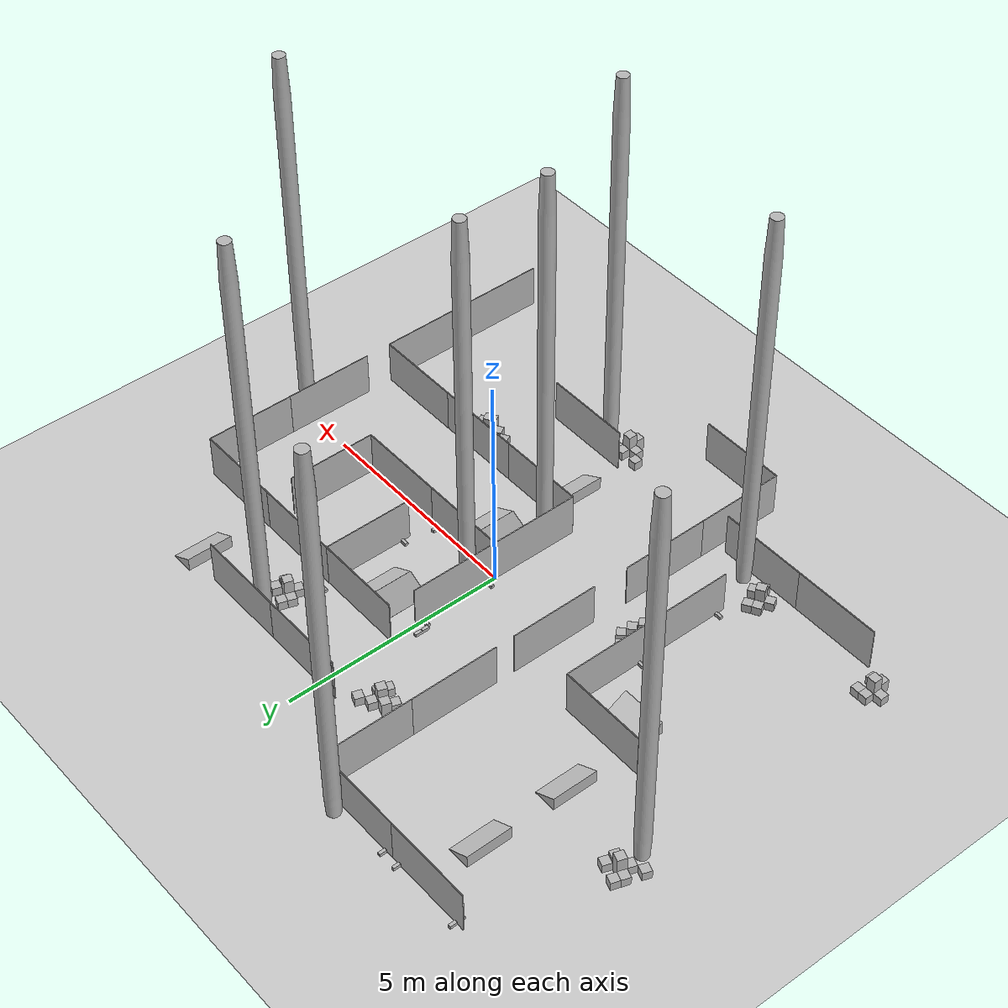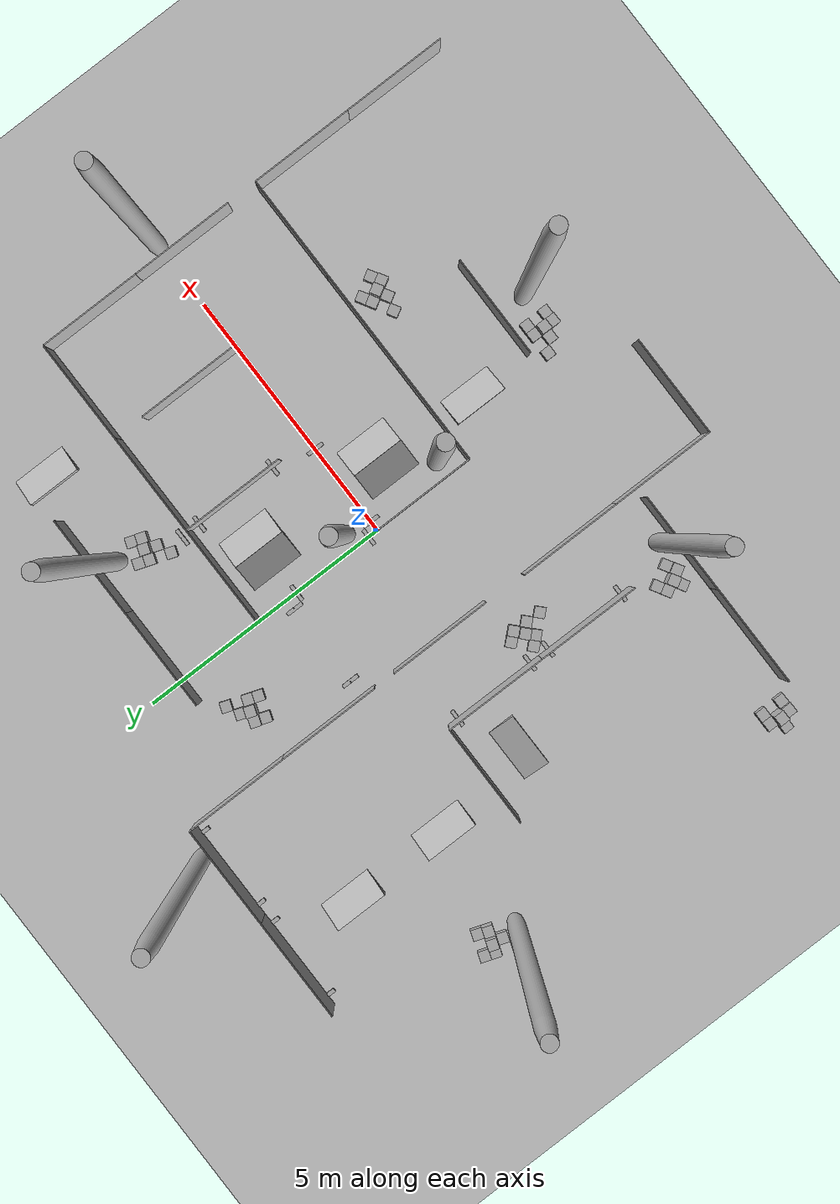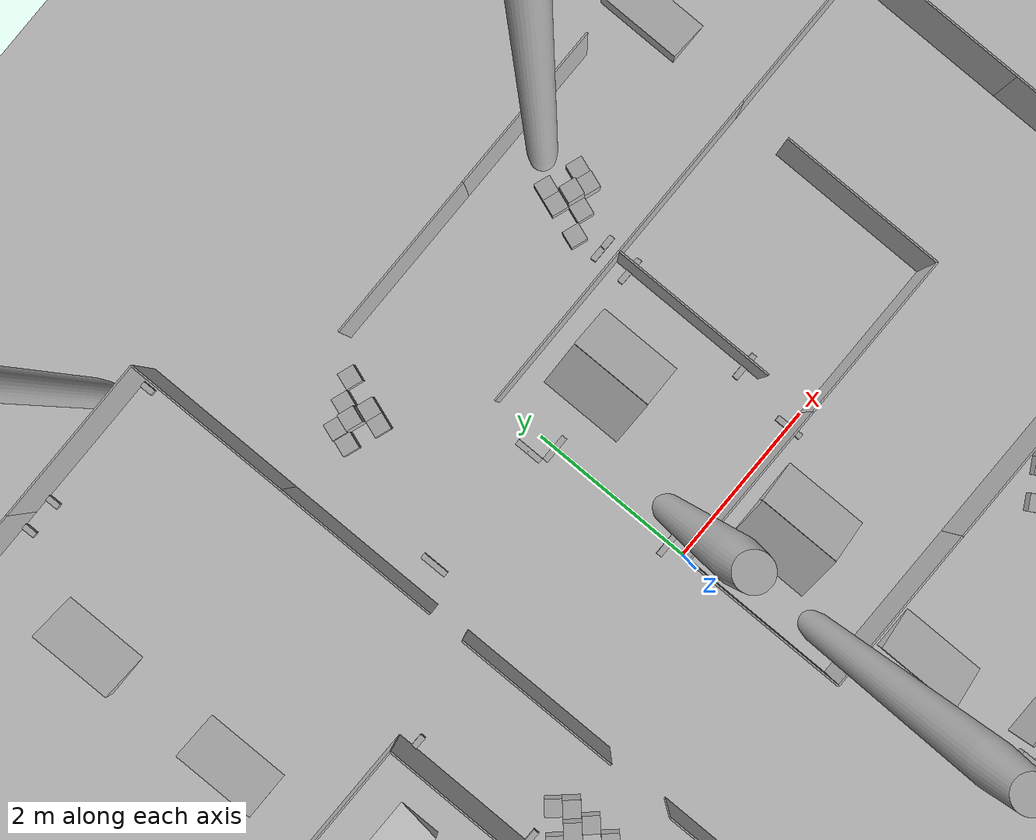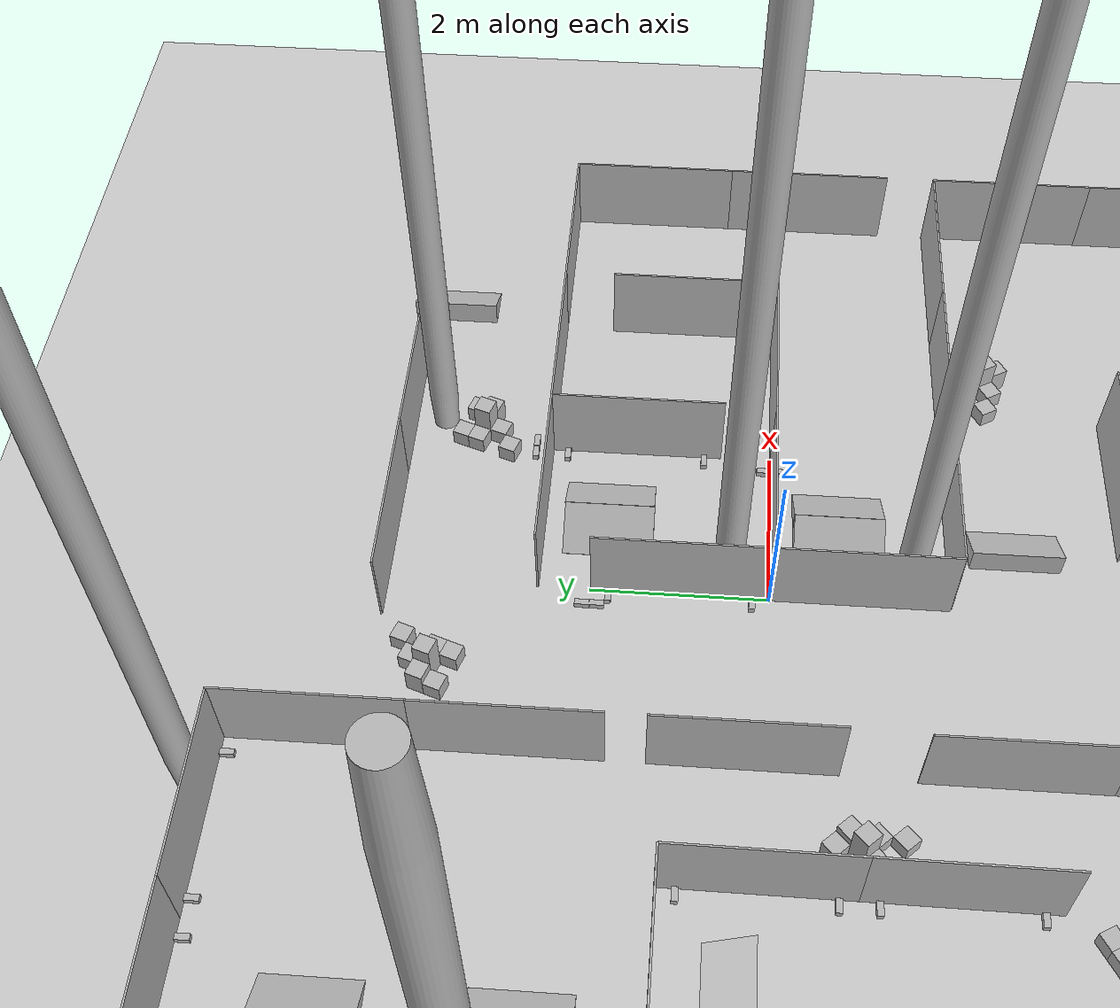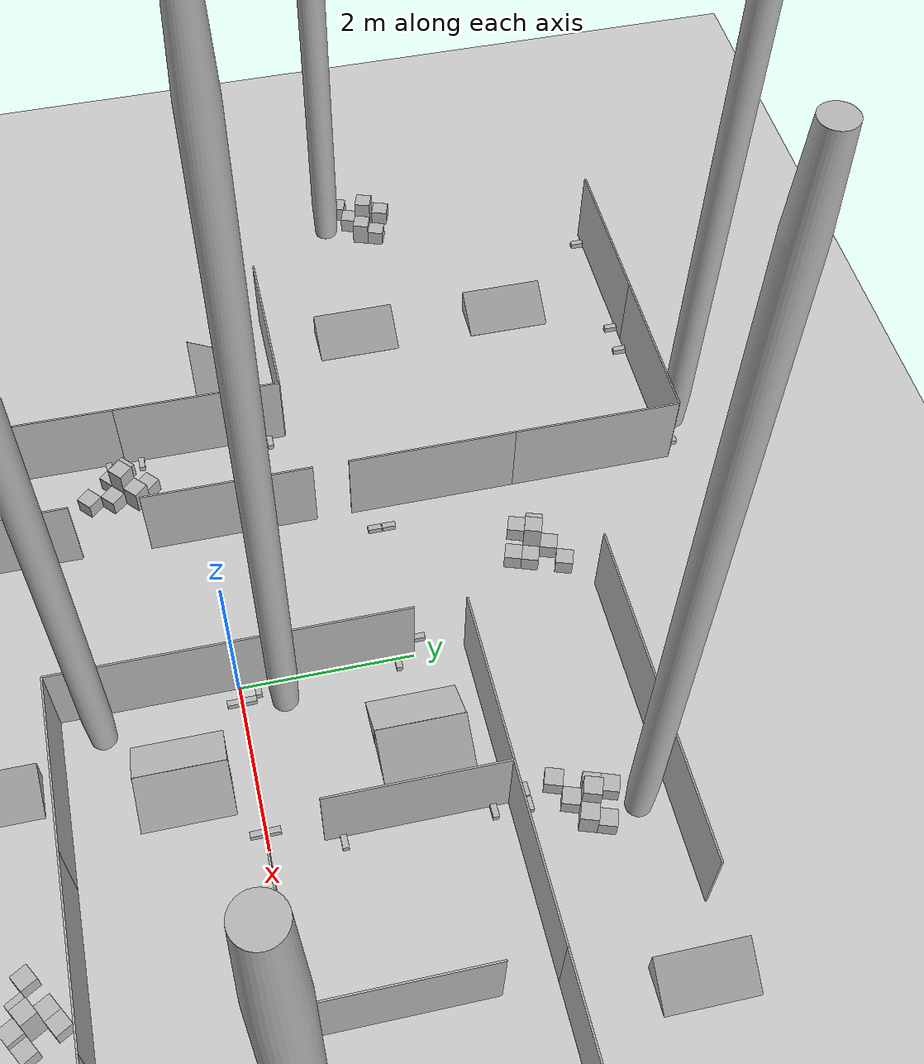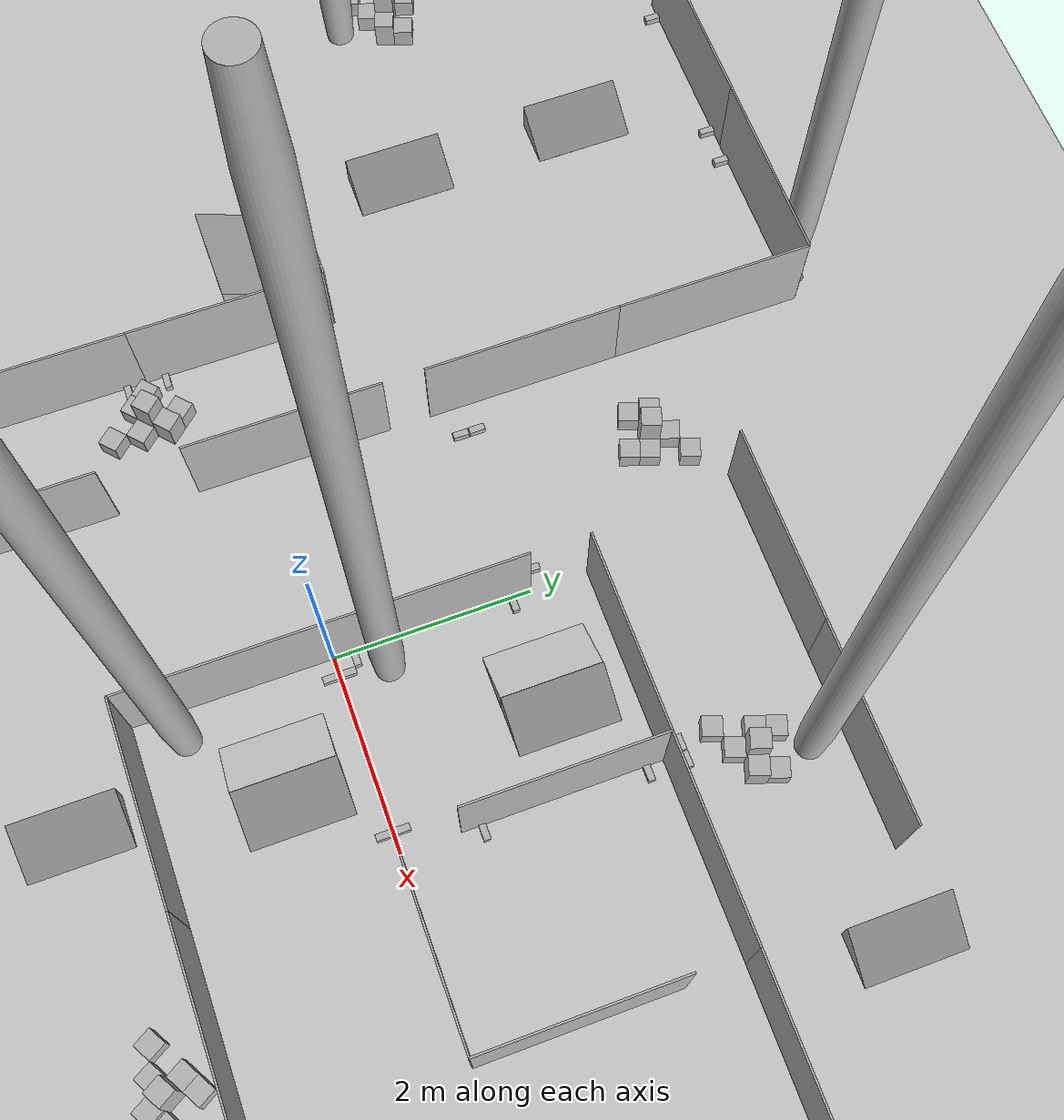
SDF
<sdf version="1.4">
  <!--Generated by blend2world.py-->
  <world name="arena_HKT_15">
    <scene>
      <ambient>0.5 0.5 0.5 1</ambient>
      <background>0.5 0.5 0.5 1</background>
      <shadows>false</shadows>
    </scene>
    <physics type="ode">
      <gravity>0 0 -9.81</gravity>
      <ode>
        <solver>
          <type>quick</type>
          <iters>1000</iters>
          <sor>1.3</sor>
        </solver>
        <constraints>
          <cfm>0.0</cfm>
          <erp>0.2</erp>
          <contact_max_correcting_vel>100.0</contact_max_correcting_vel>
          <contact_surface_layer>0.001</contact_surface_layer>
        </constraints>
      </ode>
      <real_time_update_rate>120</real_time_update_rate>
      <real_time_factor>1</real_time_factor>
      <max_step_size>0.008333</max_step_size>
    </physics>
    <light name="directional_light_1" type="directional">
      <cast_shadows>false</cast_shadows>
      <pose>0 0 30 0.1 0.1 0</pose>
      <diffuse>1.0 1.0 1.0 1</diffuse>
      <specular>.1 .1 .1 1</specular>
      <attenuation>
        <range>300</range>
      </attenuation>
      <direction>0.1 0.1 -1</direction>
    </light>
    <include>
      <uri>model://ground_plane</uri>
    </include>
    <light name="directional_light.-10.0_-12.0" type="sun">
      <pose>-10.0 -12.0 8  0 0 0</pose>
      <cast_shadows>1</cast_shadows>
      <diffuse>0.5 0.5 0.5 1</diffuse>
      <specular>0.1 0.1 0.1 1</specular>
      <attenuation>
        <range>20</range>
        <constant>0.5</constant>
        <linear>0.01</linear>
        <quadratic>0.00</quadratic>
      </attenuation>
      <direction>0.1 0.1 -1.0</direction>
    </light>
    <light name="directional_light.-10.0_0.0" type="sun">
      <pose>-10.0 0.0 8  0 0 0</pose>
      <cast_shadows>1</cast_shadows>
      <diffuse>0.5 0.5 0.5 1</diffuse>
      <specular>0.1 0.1 0.1 1</specular>
      <attenuation>
        <range>20</range>
        <constant>0.5</constant>
        <linear>0.01</linear>
        <quadratic>0.00</quadratic>
      </attenuation>
      <direction>0.1 0.1 -1.0</direction>
    </light>
    <light name="directional_light.-10.0_12.0" type="sun">
      <pose>-10.0 12.0 8  0 0 0</pose>
      <cast_shadows>1</cast_shadows>
      <diffuse>0.5 0.5 0.5 1</diffuse>
      <specular>0.1 0.1 0.1 1</specular>
      <attenuation>
        <range>20</range>
        <constant>0.5</constant>
        <linear>0.01</linear>
        <quadratic>0.00</quadratic>
      </attenuation>
      <direction>0.1 0.1 -1.0</direction>
    </light>
    <light name="directional_light.0.0_-12.0" type="sun">
      <pose>0.0 -12.0 8  0 0 0</pose>
      <cast_shadows>1</cast_shadows>
      <diffuse>0.5 0.5 0.5 1</diffuse>
      <specular>0.1 0.1 0.1 1</specular>
      <attenuation>
        <range>20</range>
        <constant>0.5</constant>
        <linear>0.01</linear>
        <quadratic>0.00</quadratic>
      </attenuation>
      <direction>0.1 0.1 -1.0</direction>
    </light>
    <light name="directional_light.0.0_0.0" type="sun">
      <pose>0.0 0.0 8  0 0 0</pose>
      <cast_shadows>1</cast_shadows>
      <diffuse>0.5 0.5 0.5 1</diffuse>
      <specular>0.1 0.1 0.1 1</specular>
      <attenuation>
        <range>20</range>
        <constant>0.5</constant>
        <linear>0.01</linear>
        <quadratic>0.00</quadratic>
      </attenuation>
      <direction>0.1 0.1 -1.0</direction>
    </light>
    <light name="directional_light.0.0_12.0" type="sun">
      <pose>0.0 12.0 8  0 0 0</pose>
      <cast_shadows>1</cast_shadows>
      <diffuse>0.5 0.5 0.5 1</diffuse>
      <specular>0.1 0.1 0.1 1</specular>
      <attenuation>
        <range>20</range>
        <constant>0.5</constant>
        <linear>0.01</linear>
        <quadratic>0.00</quadratic>
      </attenuation>
      <direction>0.1 0.1 -1.0</direction>
    </light>
    <light name="directional_light.10.0_-12.0" type="sun">
      <pose>10.0 -12.0 8  0 0 0</pose>
      <cast_shadows>1</cast_shadows>
      <diffuse>0.5 0.5 0.5 1</diffuse>
      <specular>0.1 0.1 0.1 1</specular>
      <attenuation>
        <range>20</range>
        <constant>0.5</constant>
        <linear>0.01</linear>
        <quadratic>0.00</quadratic>
      </attenuation>
      <direction>0.1 0.1 -1.0</direction>
    </light>
    <light name="directional_light.10.0_0.0" type="sun">
      <pose>10.0 0.0 8  0 0 0</pose>
      <cast_shadows>1</cast_shadows>
      <diffuse>0.5 0.5 0.5 1</diffuse>
      <specular>0.1 0.1 0.1 1</specular>
      <attenuation>
        <range>20</range>
        <constant>0.5</constant>
        <linear>0.01</linear>
        <quadratic>0.00</quadratic>
      </attenuation>
      <direction>0.1 0.1 -1.0</direction>
    </light>
    <light name="directional_light.10.0_12.0" type="sun">
      <pose>10.0 12.0 8  0 0 0</pose>
      <cast_shadows>1</cast_shadows>
      <diffuse>0.5 0.5 0.5 1</diffuse>
      <specular>0.1 0.1 0.1 1</specular>
      <attenuation>
        <range>20</range>
        <constant>0.5</constant>
        <linear>0.01</linear>
        <quadratic>0.00</quadratic>
      </attenuation>
      <direction>0.1 0.1 -1.0</direction>
    </light>
    <include>
      <name>barrel_110l.112</name>
      <pose>-6.8987884521484375 2.282184362411499 0.0  0.0 0.0 0.0</pose>
      <uri>model://barrel_110l</uri>
    </include>
    <include>
      <name>barrel_110l.113</name>
      <pose>-2.648716449737549 5.911823272705078 0.0  0.0 0.0 0.0</pose>
      <uri>model://barrel_110l</uri>
    </include>
    <include>
      <name>barrel_110l.114</name>
      <pose>2.3416879177093506 3.916957378387451 0.0  0.0 0.0 0.0</pose>
      <uri>model://barrel_110l</uri>
    </include>
    <include>
      <name>barrel_110l.115</name>
      <pose>1.6949834823608398 -4.506519794464111 0.0  0.0 0.0 0.0</pose>
      <uri>model://barrel_110l</uri>
    </include>
    <include>
      <name>barrel_110l.116</name>
      <pose>0.32114124298095703 -1.5364108085632324 0.0  0.0 0.0 0.0</pose>
      <uri>model://barrel_110l</uri>
    </include>
    <include>
      <name>barrel_110l.117</name>
      <pose>6.263016223907471 -0.004051387310028076 0.0  0.0 0.0 0.0</pose>
      <uri>model://barrel_110l</uri>
    </include>
    <include>
      <name>barrel_110l.118</name>
      <pose>0.2812814712524414 0.4758661985397339 0.0  0.0 0.0 0.0</pose>
      <uri>model://barrel_110l</uri>
    </include>
    <include>
      <name>barrel_110l.119</name>
      <pose>-3.1529698371887207 -3.7413508892059326 0.0  0.0 0.0 0.0</pose>
      <uri>model://barrel_110l</uri>
    </include>
    <include>
      <name>cube_20x20.1554</name>
      <pose>1.0329742431640625 -4.255204200744629 0.10000000149011612  0.0 -0.0 3.141592502593994</pose>
      <uri>model://cube_20x20</uri>
    </include>
    <include>
      <name>cube_20x20.1555</name>
      <pose>0.8329744338989258 -4.455204010009766 0.10000000149011612  0.0 -0.0 3.141592502593994</pose>
      <uri>model://cube_20x20</uri>
    </include>
    <include>
      <name>cube_20x20.1556</name>
      <pose>0.6329746246337891 -4.255204200744629 0.10000000149011612  0.0 -0.0 3.141592502593994</pose>
      <uri>model://cube_20x20</uri>
    </include>
    <include>
      <name>cube_20x20.1557</name>
      <pose>1.2329745292663574 -4.255204200744629 0.10000000149011612  0.0 -0.0 3.141592502593994</pose>
      <uri>model://cube_20x20</uri>
    </include>
    <include>
      <name>cube_20x20.1558</name>
      <pose>1.2329745292663574 -4.655203819274902 0.10000000149011612  0.0 -0.0 3.141592502593994</pose>
      <uri>model://cube_20x20</uri>
    </include>
    <include>
      <name>cube_20x20.1559</name>
      <pose>1.0329742431640625 -4.255204200744629 0.10000000149011612  0.0 -0.0 3.141592502593994</pose>
      <uri>model://cube_20x20</uri>
    </include>
    <include>
      <name>cube_20x20.1560</name>
      <pose>0.8329744338989258 -4.455204010009766 0.10000000149011612  0.0 -0.0 3.141592502593994</pose>
      <uri>model://cube_20x20</uri>
    </include>
    <include>
      <name>cube_20x20.1561</name>
      <pose>0.6329746246337891 -4.255204200744629 0.10000000149011612  0.0 -0.0 3.141592502593994</pose>
      <uri>model://cube_20x20</uri>
    </include>
    <include>
      <name>cube_20x20.1562</name>
      <pose>1.2329745292663574 -4.255204200744629 0.10000000149011612  0.0 -0.0 3.141592502593994</pose>
      <uri>model://cube_20x20</uri>
    </include>
    <include>
      <name>cube_20x20.1563</name>
      <pose>1.2329745292663574 -4.655203819274902 0.10000000149011612  0.0 -0.0 3.141592502593994</pose>
      <uri>model://cube_20x20</uri>
    </include>
    <include>
      <name>cube_20x20.1564</name>
      <pose>-6.874878406524658 -3.3630831241607666 0.10000000149011612  0.0 -0.0 3.141592502593994</pose>
      <uri>model://cube_20x20</uri>
    </include>
    <include>
      <name>cube_20x20.1565</name>
      <pose>-7.074878215789795 -3.5630829334259033 0.10000000149011612  0.0 -0.0 3.141592502593994</pose>
      <uri>model://cube_20x20</uri>
    </include>
    <include>
      <name>cube_20x20.1566</name>
      <pose>-6.674878120422363 -3.3630831241607666 0.10000000149011612  0.0 -0.0 3.141592502593994</pose>
      <uri>model://cube_20x20</uri>
    </include>
    <include>
      <name>cube_20x20.1567</name>
      <pose>-6.674878120422363 -3.76308274269104 0.10000000149011612  0.0 -0.0 3.141592502593994</pose>
      <uri>model://cube_20x20</uri>
    </include>
    <include>
      <name>cube_20x20.1568</name>
      <pose>-6.874878406524658 -3.3630831241607666 0.10000000149011612  0.0 -0.0 3.141592502593994</pose>
      <uri>model://cube_20x20</uri>
    </include>
    <include>
      <name>cube_20x20.1569</name>
      <pose>-7.074878215789795 -3.5630829334259033 0.10000000149011612  0.0 -0.0 3.141592502593994</pose>
      <uri>model://cube_20x20</uri>
    </include>
    <include>
      <name>cube_20x20.1570</name>
      <pose>-6.674878120422363 -3.3630831241607666 0.10000000149011612  0.0 -0.0 3.141592502593994</pose>
      <uri>model://cube_20x20</uri>
    </include>
    <include>
      <name>cube_20x20.1571</name>
      <pose>-6.674878120422363 -3.76308274269104 0.10000000149011612  0.0 -0.0 3.141592502593994</pose>
      <uri>model://cube_20x20</uri>
    </include>
    <include>
      <name>cube_20x20.1572</name>
      <pose>-3.9385533332824707 -3.3717634677886963 0.10000000149011612  0.0 -0.0 3.6651763916015625</pose>
      <uri>model://cube_20x20</uri>
    </include>
    <include>
      <name>cube_20x20.1573</name>
      <pose>-4.011762619018555 -3.6449673175811768 0.10000000149011612  0.0 -0.0 3.6651763916015625</pose>
      <uri>model://cube_20x20</uri>
    </include>
    <include>
      <name>cube_20x20.1574</name>
      <pose>-3.7653465270996094 -3.271765947341919 0.10000000149011612  0.0 -0.0 3.6651763916015625</pose>
      <uri>model://cube_20x20</uri>
    </include>
    <include>
      <name>cube_20x20.1575</name>
      <pose>-3.565351963043213 -3.6181790828704834 0.10000000149011612  0.0 -0.0 3.6651763916015625</pose>
      <uri>model://cube_20x20</uri>
    </include>
    <include>
      <name>cube_20x20.1576</name>
      <pose>-3.9385533332824707 -3.3717634677886963 0.10000000149011612  0.0 -0.0 3.6651763916015625</pose>
      <uri>model://cube_20x20</uri>
    </include>
    <include>
      <name>cube_20x20.1577</name>
      <pose>-4.011762619018555 -3.6449673175811768 0.10000000149011612  0.0 -0.0 3.6651763916015625</pose>
      <uri>model://cube_20x20</uri>
    </include>
    <include>
      <name>cube_20x20.1578</name>
      <pose>-3.7653465270996094 -3.271765947341919 0.10000000149011612  0.0 -0.0 3.6651763916015625</pose>
      <uri>model://cube_20x20</uri>
    </include>
    <include>
      <name>cube_20x20.1579</name>
      <pose>-3.565351963043213 -3.6181790828704834 0.10000000149011612  0.0 -0.0 3.6651763916015625</pose>
      <uri>model://cube_20x20</uri>
    </include>
    <include>
      <name>cube_20x20.1580</name>
      <pose>-3.1368727684020996 -1.071094274520874 0.10000000149011612  0.0 0.0 5.4528021812438965</pose>
      <uri>model://cube_20x20</uri>
    </include>
    <include>
      <name>cube_20x20.1581</name>
      <pose>-2.8543167114257812 -1.0838134288787842 0.10000000149011612  0.0 0.0 5.4528021812438965</pose>
      <uri>model://cube_20x20</uri>
    </include>
    <include>
      <name>cube_20x20.1582</name>
      <pose>-2.8670363426208496 -1.3663697242736816 0.10000000149011612  0.0 0.0 5.4528021812438965</pose>
      <uri>model://cube_20x20</uri>
    </include>
    <include>
      <name>cube_20x20.1583</name>
      <pose>-3.2717912197113037 -0.9234559535980225 0.10000000149011612  0.0 0.0 5.4528021812438965</pose>
      <uri>model://cube_20x20</uri>
    </include>
    <include>
      <name>cube_20x20.1584</name>
      <pose>-2.976515293121338 -0.6536192893981934 0.10000000149011612  0.0 0.0 5.4528021812438965</pose>
      <uri>model://cube_20x20</uri>
    </include>
    <include>
      <name>cube_20x20.1585</name>
      <pose>-3.1368727684020996 -1.071094274520874 0.10000000149011612  0.0 0.0 5.4528021812438965</pose>
      <uri>model://cube_20x20</uri>
    </include>
    <include>
      <name>cube_20x20.1586</name>
      <pose>-2.8543167114257812 -1.0838134288787842 0.10000000149011612  0.0 0.0 5.4528021812438965</pose>
      <uri>model://cube_20x20</uri>
    </include>
    <include>
      <name>cube_20x20.1587</name>
      <pose>-2.8670363426208496 -1.3663697242736816 0.10000000149011612  0.0 0.0 5.4528021812438965</pose>
      <uri>model://cube_20x20</uri>
    </include>
    <include>
      <name>cube_20x20.1588</name>
      <pose>-3.2717912197113037 -0.9234559535980225 0.10000000149011612  0.0 0.0 5.4528021812438965</pose>
      <uri>model://cube_20x20</uri>
    </include>
    <include>
      <name>cube_20x20.1589</name>
      <pose>-2.976515293121338 -0.6536192893981934 0.10000000149011612  0.0 0.0 5.4528021812438965</pose>
      <uri>model://cube_20x20</uri>
    </include>
    <include>
      <name>cube_20x30.282</name>
      <pose>1.0329742431640625 -4.655203819274902 0.15000000596046448  0.0 -0.0 3.141592502593994</pose>
      <uri>model://cube_20x30</uri>
    </include>
    <include>
      <name>cube_20x30.283</name>
      <pose>1.0329742431640625 -4.655203819274902 0.15000000596046448  0.0 -0.0 3.141592502593994</pose>
      <uri>model://cube_20x30</uri>
    </include>
    <include>
      <name>cube_20x30.284</name>
      <pose>-6.874878406524658 -3.76308274269104 0.15000000596046448  0.0 -0.0 3.141592502593994</pose>
      <uri>model://cube_20x30</uri>
    </include>
    <include>
      <name>cube_20x30.285</name>
      <pose>-6.874878406524658 -3.76308274269104 0.15000000596046448  0.0 -0.0 3.141592502593994</pose>
      <uri>model://cube_20x30</uri>
    </include>
    <include>
      <name>cube_20x30.286</name>
      <pose>-3.738558769226074 -3.7181766033172607 0.15000000596046448  0.0 -0.0 3.6651763916015625</pose>
      <uri>model://cube_20x30</uri>
    </include>
    <include>
      <name>cube_20x30.287</name>
      <pose>-3.738558769226074 -3.7181766033172607 0.15000000596046448  0.0 -0.0 3.6651763916015625</pose>
      <uri>model://cube_20x30</uri>
    </include>
    <include>
      <name>cube_20x30.288</name>
      <pose>-2.841596841812134 -0.8012573719024658 0.15000000596046448  0.0 0.0 5.4528021812438965</pose>
      <uri>model://cube_20x30</uri>
    </include>
    <include>
      <name>cube_20x30.289</name>
      <pose>-2.841596841812134 -0.8012573719024658 0.15000000596046448  0.0 0.0 5.4528021812438965</pose>
      <uri>model://cube_20x30</uri>
    </include>
    <include>
      <name>cube_20x50.276</name>
      <pose>1.0329742431640625 -4.455204010009766 0.25  0.0 -0.0 3.141592502593994</pose>
      <uri>model://cube_20x50</uri>
    </include>
    <include>
      <name>cube_20x50.277</name>
      <pose>1.0329742431640625 -4.455204010009766 0.25  0.0 -0.0 3.141592502593994</pose>
      <uri>model://cube_20x50</uri>
    </include>
    <include>
      <name>cube_20x50.278</name>
      <pose>-6.874878406524658 -3.5630829334259033 0.25  0.0 -0.0 3.141592502593994</pose>
      <uri>model://cube_20x50</uri>
    </include>
    <include>
      <name>cube_20x50.279</name>
      <pose>-6.874878406524658 -3.5630829334259033 0.25  0.0 -0.0 3.141592502593994</pose>
      <uri>model://cube_20x50</uri>
    </include>
    <include>
      <name>cube_20x50.280</name>
      <pose>-3.8385560512542725 -3.5449702739715576 0.25  0.0 -0.0 3.6651763916015625</pose>
      <uri>model://cube_20x50</uri>
    </include>
    <include>
      <name>cube_20x50.281</name>
      <pose>-3.8385560512542725 -3.5449702739715576 0.25  0.0 -0.0 3.6651763916015625</pose>
      <uri>model://cube_20x50</uri>
    </include>
    <include>
      <name>cube_20x50.282</name>
      <pose>-2.989234209060669 -0.9361758232116699 0.25  0.0 0.0 5.4528021812438965</pose>
      <uri>model://cube_20x50</uri>
    </include>
    <include>
      <name>cube_20x50.283</name>
      <pose>-2.989234209060669 -0.9361758232116699 0.25  0.0 0.0 5.4528021812438965</pose>
      <uri>model://cube_20x50</uri>
    </include>
    <include>
      <name>ramp.135</name>
      <pose>-4.520613670349121 0.37118804454803467 0.15000000596046448  0.0 -0.0 7.853981971740723</pose>
      <uri>model://ramp</uri>
    </include>
    <include>
      <name>ramp.136</name>
      <pose>0.8559532165527344 -2.760223627090454 0.15000000596046448  0.0 -0.0 6.283185005187988</pose>
      <uri>model://ramp</uri>
    </include>
    <include>
      <name>ramp.137</name>
      <pose>-4.8568115234375 2.3036534786224365 0.15000000596046448  0.0 -0.0 6.283185005187988</pose>
      <uri>model://ramp</uri>
    </include>
    <include>
      <name>ramp.138</name>
      <pose>-4.8568115234375 4.303653717041016 0.15000000596046448  0.0 -0.0 6.283185005187988</pose>
      <uri>model://ramp</uri>
    </include>
    <include>
      <name>wall_2x1.610</name>
      <pose>-3.476762056350708 -1.890228271484375 0.5130000114440918  0.0 -0.0 4.708364486694336</pose>
      <uri>model://wall_2x1</uri>
    </include>
    <include>
      <name>wall_2x1.611</name>
      <pose>1.8000993728637695 -3.9420547485351562 0.5130000114440918  0.0 -0.0 3.1375677585601807</pose>
      <uri>model://wall_2x1</uri>
    </include>
    <include>
      <name>wall_stand.1331</name>
      <pose>-1.8005000352859497 2.0 0.03449999913573265  0.0 -0.0 1.570796251296997</pose>
      <uri>model://wall_stand</uri>
    </include>
    <include>
      <name>wall_stand.1332</name>
      <pose>-0.19949999451637268 2.0 0.03449999913573265  0.0 -0.0 1.570796251296997</pose>
      <uri>model://wall_stand</uri>
    </include>
    <include>
      <name>wall_2x1.612</name>
      <pose>-3.468712091445923 0.1097555160522461 0.5130000114440918  0.0 -0.0 4.708364486694336</pose>
      <uri>model://wall_2x1</uri>
    </include>
    <include>
      <name>wall_2x1.613</name>
      <pose>-4.464678764343262 1.1137723922729492 0.5130000114440918  0.0 -0.0 3.1375677585601807</pose>
      <uri>model://wall_2x1</uri>
    </include>
    <include>
      <name>wall_stand.1333</name>
      <pose>-0.19949999451637268 2.0 0.03449999913573265  0.0 -0.0 1.570796251296997</pose>
      <uri>model://wall_stand</uri>
    </include>
    <include>
      <name>wall_2x1.614</name>
      <pose>-2.147331953048706 -2.5302858352661133 0.5130000114440918  0.0 -0.0 1.570796251296997</pose>
      <uri>model://wall_2x1</uri>
    </include>
    <include>
      <name>wall_stand.1334</name>
      <pose>-1.8005000352859497 2.0 0.03449999913573265  0.0 -0.0 1.570796251296997</pose>
      <uri>model://wall_stand</uri>
    </include>
    <include>
      <name>wall_stand.1335</name>
      <pose>-0.19949999451637268 2.0 0.03449999913573265  0.0 -0.0 1.570796251296997</pose>
      <uri>model://wall_stand</uri>
    </include>
    <include>
      <name>wall_2x1.615</name>
      <pose>-1.1473321914672852 -5.530285835266113 0.5130000114440918  0.0 -0.0 3.141592502593994</pose>
      <uri>model://wall_2x1</uri>
    </include>
    <include>
      <name>wall_2x1.616</name>
      <pose>-2.147332191467285 -4.530285835266113 0.5130000114440918  0.0 -0.0 1.570796251296997</pose>
      <uri>model://wall_2x1</uri>
    </include>
    <include>
      <name>wall_stand.1336</name>
      <pose>-0.19949999451637268 2.0 0.03449999913573265  0.0 -0.0 1.570796251296997</pose>
      <uri>model://wall_stand</uri>
    </include>
    <include>
      <name>wall_2x1.617</name>
      <pose>-2.1166141033172607 2.695002794265747 0.5130000114440918  0.0 -0.0 4.71238899230957</pose>
      <uri>model://wall_2x1</uri>
    </include>
    <include>
      <name>wall_stand.1337</name>
      <pose>-1.8005000352859497 2.0 0.03449999913573265  0.0 -0.0 1.570796251296997</pose>
      <uri>model://wall_stand</uri>
    </include>
    <include>
      <name>wall_stand.1338</name>
      <pose>-0.19949999451637268 2.0 0.03449999913573265  0.0 -0.0 1.570796251296997</pose>
      <uri>model://wall_stand</uri>
    </include>
    <include>
      <name>wall_2x1.618</name>
      <pose>-5.116613388061523 5.695002555847168 0.5130000114440918  0.0 -0.0 6.283185005187988</pose>
      <uri>model://wall_2x1</uri>
    </include>
    <include>
      <name>wall_2x1.619</name>
      <pose>-3.1166136264801025 5.695002555847168 0.5130000114440918  0.0 -0.0 6.283185005187988</pose>
      <uri>model://wall_2x1</uri>
    </include>
    <include>
      <name>wall_2x1.620</name>
      <pose>-2.1166136264801025 4.695002555847168 0.5130000114440918  0.0 -0.0 4.71238899230957</pose>
      <uri>model://wall_2x1</uri>
    </include>
    <include>
      <name>wall_stand.1339</name>
      <pose>-0.19949999451637268 2.0 0.03449999913573265  0.0 -0.0 1.570796251296997</pose>
      <uri>model://wall_stand</uri>
    </include>
    <include>
      <name>wall_2x1.621</name>
      <pose>-2.1166141033172607 0.2739219665527344 0.5130000114440918  0.0 -0.0 4.71238899230957</pose>
      <uri>model://wall_2x1</uri>
    </include>
    <include>
      <name>wall_stand.1340</name>
      <pose>-1.8005000352859497 2.0 0.03449999913573265  0.0 -0.0 1.570796251296997</pose>
      <uri>model://wall_stand</uri>
    </include>
    <include>
      <name>wall_stand.1341</name>
      <pose>-0.19949999451637268 2.0 0.03449999913573265  0.0 -0.0 1.570796251296997</pose>
      <uri>model://wall_stand</uri>
    </include>
    <include>
      <name>wall_stand.1342</name>
      <pose>-3.4799840450286865 -2.6907219886779785 0.03450000286102295  0.0 -0.0 3.1375677585601807</pose>
      <uri>model://wall_stand</uri>
    </include>
    <include>
      <name>wall_stand.1343</name>
      <pose>-3.4735400676727295 -1.0897347927093506 0.03450000286102295  0.0 -0.0 3.1375677585601807</pose>
      <uri>model://wall_stand</uri>
    </include>
    <include>
      <name>wall_stand.1344</name>
      <pose>-3.4719340801239014 -0.6907380819320679 0.03450000286102295  0.0 -0.0 3.1375677585601807</pose>
      <uri>model://wall_stand</uri>
    </include>
    <include>
      <name>wall_stand.1345</name>
      <pose>-3.4654901027679443 0.9102489948272705 0.03450000286102295  0.0 -0.0 3.1375677585601807</pose>
      <uri>model://wall_stand</uri>
    </include>
    <include>
      <name>wall_stand.1346</name>
      <pose>-5.917113304138184 5.695002555847168 0.03450000286102295  0.0 -0.0 4.71238899230957</pose>
      <uri>model://wall_stand</uri>
    </include>
    <include>
      <name>wall_stand.1347</name>
      <pose>-4.316113471984863 5.695002555847168 0.03450000286102295  0.0 -0.0 4.71238899230957</pose>
      <uri>model://wall_stand</uri>
    </include>
    <include>
      <name>wall_stand.1348</name>
      <pose>-2.316113233566284 5.695002555847168 0.03450000286102295  0.0 -0.0 4.71238899230957</pose>
      <uri>model://wall_stand</uri>
    </include>
    <include>
      <name>wall_stand.1349</name>
      <pose>-3.9171135425567627 5.695002555847168 0.03450000286102295  0.0 -0.0 4.71238899230957</pose>
      <uri>model://wall_stand</uri>
    </include>
    <include>
      <name>cube_20x20.1590</name>
      <pose>2.0343916416168213 3.479175329208374 0.10000000149011612  0.0 0.0 4.376082897186279</pose>
      <uri>model://cube_20x20</uri>
    </include>
    <include>
      <name>cube_20x20.1591</name>
      <pose>2.1571874618530273 3.224379301071167 0.10000000149011612  0.0 0.0 4.376082897186279</pose>
      <uri>model://cube_20x20</uri>
    </include>
    <include>
      <name>cube_20x20.1592</name>
      <pose>1.902390956878662 3.1015841960906982 0.10000000149011612  0.0 0.0 4.376082897186279</pose>
      <uri>model://cube_20x20</uri>
    </include>
    <include>
      <name>cube_20x20.1593</name>
      <pose>2.1003925800323486 3.66797137260437 0.10000000149011612  0.0 0.0 4.376082897186279</pose>
      <uri>model://cube_20x20</uri>
    </include>
    <include>
      <name>cube_20x20.1594</name>
      <pose>2.4779841899871826 3.535970449447632 0.10000000149011612  0.0 0.0 4.376082897186279</pose>
      <uri>model://cube_20x20</uri>
    </include>
    <include>
      <name>cube_20x20.1595</name>
      <pose>2.0343916416168213 3.479175329208374 0.10000000149011612  0.0 0.0 4.376082897186279</pose>
      <uri>model://cube_20x20</uri>
    </include>
    <include>
      <name>cube_20x20.1596</name>
      <pose>2.1571874618530273 3.224379301071167 0.10000000149011612  0.0 0.0 4.376082897186279</pose>
      <uri>model://cube_20x20</uri>
    </include>
    <include>
      <name>cube_20x20.1597</name>
      <pose>1.902390956878662 3.1015841960906982 0.10000000149011612  0.0 0.0 4.376082897186279</pose>
      <uri>model://cube_20x20</uri>
    </include>
    <include>
      <name>cube_20x20.1598</name>
      <pose>2.1003925800323486 3.66797137260437 0.10000000149011612  0.0 0.0 4.376082897186279</pose>
      <uri>model://cube_20x20</uri>
    </include>
    <include>
      <name>cube_20x20.1599</name>
      <pose>2.4779841899871826 3.535970449447632 0.10000000149011612  0.0 0.0 4.376082897186279</pose>
      <uri>model://cube_20x20</uri>
    </include>
    <include>
      <name>cube_20x20.1600</name>
      <pose>-0.9480915069580078 3.6092355251312256 0.10000000149011612  0.0 0.0 7.517675399780273</pose>
      <uri>model://cube_20x20</uri>
    </include>
    <include>
      <name>cube_20x20.1601</name>
      <pose>-1.0708873271942139 3.8640315532684326 0.10000000149011612  0.0 0.0 7.517675399780273</pose>
      <uri>model://cube_20x20</uri>
    </include>
    <include>
      <name>cube_20x20.1602</name>
      <pose>-0.8160908222198486 3.9868276119232178 0.10000000149011612  0.0 0.0 7.517675399780273</pose>
      <uri>model://cube_20x20</uri>
    </include>
    <include>
      <name>cube_20x20.1603</name>
      <pose>-1.0140924453735352 3.4204394817352295 0.10000000149011612  0.0 0.0 7.517675399780273</pose>
      <uri>model://cube_20x20</uri>
    </include>
    <include>
      <name>cube_20x20.1604</name>
      <pose>-1.3916840553283691 3.5524404048919678 0.10000000149011612  0.0 0.0 7.517675399780273</pose>
      <uri>model://cube_20x20</uri>
    </include>
    <include>
      <name>cube_20x20.1605</name>
      <pose>-0.9480915069580078 3.6092355251312256 0.10000000149011612  0.0 0.0 7.517675399780273</pose>
      <uri>model://cube_20x20</uri>
    </include>
    <include>
      <name>cube_20x20.1606</name>
      <pose>-1.0708873271942139 3.8640315532684326 0.10000000149011612  0.0 0.0 7.517675399780273</pose>
      <uri>model://cube_20x20</uri>
    </include>
    <include>
      <name>cube_20x20.1607</name>
      <pose>-0.8160908222198486 3.9868276119232178 0.10000000149011612  0.0 0.0 7.517675399780273</pose>
      <uri>model://cube_20x20</uri>
    </include>
    <include>
      <name>cube_20x20.1608</name>
      <pose>-1.0140924453735352 3.4204394817352295 0.10000000149011612  0.0 0.0 7.517675399780273</pose>
      <uri>model://cube_20x20</uri>
    </include>
    <include>
      <name>cube_20x20.1609</name>
      <pose>-1.3916840553283691 3.5524404048919678 0.10000000149011612  0.0 0.0 7.517675399780273</pose>
      <uri>model://cube_20x20</uri>
    </include>
    <include>
      <name>cube_20x20.1610</name>
      <pose>3.2194247245788574 -2.3717634677886963 0.10000000149011612  0.0 -0.0 3.6651763916015625</pose>
      <uri>model://cube_20x20</uri>
    </include>
    <include>
      <name>cube_20x20.1611</name>
      <pose>3.1462156772613525 -2.6449673175811768 0.10000000149011612  0.0 -0.0 3.6651763916015625</pose>
      <uri>model://cube_20x20</uri>
    </include>
    <include>
      <name>cube_20x20.1612</name>
      <pose>2.873011827468872 -2.5717580318450928 0.10000000149011612  0.0 -0.0 3.6651763916015625</pose>
      <uri>model://cube_20x20</uri>
    </include>
    <include>
      <name>cube_20x20.1613</name>
      <pose>3.3926315307617188 -2.271765947341919 0.10000000149011612  0.0 -0.0 3.6651763916015625</pose>
      <uri>model://cube_20x20</uri>
    </include>
    <include>
      <name>cube_20x20.1614</name>
      <pose>3.5926260948181152 -2.6181790828704834 0.10000000149011612  0.0 -0.0 3.6651763916015625</pose>
      <uri>model://cube_20x20</uri>
    </include>
    <include>
      <name>cube_20x20.1615</name>
      <pose>3.2194247245788574 -2.3717634677886963 0.10000000149011612  0.0 -0.0 3.6651763916015625</pose>
      <uri>model://cube_20x20</uri>
    </include>
    <include>
      <name>cube_20x20.1616</name>
      <pose>3.1462156772613525 -2.6449673175811768 0.10000000149011612  0.0 -0.0 3.6651763916015625</pose>
      <uri>model://cube_20x20</uri>
    </include>
    <include>
      <name>cube_20x20.1617</name>
      <pose>2.873011827468872 -2.5717580318450928 0.10000000149011612  0.0 -0.0 3.6651763916015625</pose>
      <uri>model://cube_20x20</uri>
    </include>
    <include>
      <name>cube_20x20.1618</name>
      <pose>3.3926315307617188 -2.271765947341919 0.10000000149011612  0.0 -0.0 3.6651763916015625</pose>
      <uri>model://cube_20x20</uri>
    </include>
    <include>
      <name>cube_20x20.1619</name>
      <pose>3.5926260948181152 -2.6181790828704834 0.10000000149011612  0.0 -0.0 3.6651763916015625</pose>
      <uri>model://cube_20x20</uri>
    </include>
    <include>
      <name>cube_20x20.1620</name>
      <pose>-7.101250648498535 2.8842883110046387 0.10000000149011612  0.0 0.0 4.376082897186279</pose>
      <uri>model://cube_20x20</uri>
    </include>
    <include>
      <name>cube_20x20.1621</name>
      <pose>-6.97845458984375 2.6294922828674316 0.10000000149011612  0.0 0.0 4.376082897186279</pose>
      <uri>model://cube_20x20</uri>
    </include>
    <include>
      <name>cube_20x20.1622</name>
      <pose>-7.233251094818115 2.5066962242126465 0.10000000149011612  0.0 0.0 4.376082897186279</pose>
      <uri>model://cube_20x20</uri>
    </include>
    <include>
      <name>cube_20x20.1623</name>
      <pose>-7.035249710083008 3.0730843544006348 0.10000000149011612  0.0 0.0 4.376082897186279</pose>
      <uri>model://cube_20x20</uri>
    </include>
    <include>
      <name>cube_20x20.1624</name>
      <pose>-6.657657623291016 2.9410834312438965 0.10000000149011612  0.0 0.0 4.376082897186279</pose>
      <uri>model://cube_20x20</uri>
    </include>
    <include>
      <name>cube_20x20.1625</name>
      <pose>-7.101250648498535 2.8842883110046387 0.10000000149011612  0.0 0.0 4.376082897186279</pose>
      <uri>model://cube_20x20</uri>
    </include>
    <include>
      <name>cube_20x20.1626</name>
      <pose>-6.97845458984375 2.6294922828674316 0.10000000149011612  0.0 0.0 4.376082897186279</pose>
      <uri>model://cube_20x20</uri>
    </include>
    <include>
      <name>cube_20x20.1627</name>
      <pose>-7.233251094818115 2.5066962242126465 0.10000000149011612  0.0 0.0 4.376082897186279</pose>
      <uri>model://cube_20x20</uri>
    </include>
    <include>
      <name>cube_20x20.1628</name>
      <pose>-7.035249710083008 3.0730843544006348 0.10000000149011612  0.0 0.0 4.376082897186279</pose>
      <uri>model://cube_20x20</uri>
    </include>
    <include>
      <name>cube_20x20.1629</name>
      <pose>-6.657657623291016 2.9410834312438965 0.10000000149011612  0.0 0.0 4.376082897186279</pose>
      <uri>model://cube_20x20</uri>
    </include>
    <include>
      <name>cube_20x30.290</name>
      <pose>2.4119834899902344 3.3471744060516357 0.15000000596046448  0.0 0.0 4.376082897186279</pose>
      <uri>model://cube_20x30</uri>
    </include>
    <include>
      <name>cube_20x30.291</name>
      <pose>2.4119834899902344 3.3471744060516357 0.15000000596046448  0.0 0.0 4.376082897186279</pose>
      <uri>model://cube_20x30</uri>
    </include>
    <include>
      <name>cube_20x30.292</name>
      <pose>-1.325683355331421 3.7412374019622803 0.15000000596046448  0.0 0.0 7.517675399780273</pose>
      <uri>model://cube_20x30</uri>
    </include>
    <include>
      <name>cube_20x30.293</name>
      <pose>-1.325683355331421 3.7412374019622803 0.15000000596046448  0.0 0.0 7.517675399780273</pose>
      <uri>model://cube_20x30</uri>
    </include>
    <include>
      <name>cube_20x30.294</name>
      <pose>3.419419288635254 -2.7181766033172607 0.15000000596046448  0.0 -0.0 3.6651763916015625</pose>
      <uri>model://cube_20x30</uri>
    </include>
    <include>
      <name>cube_20x30.295</name>
      <pose>3.419419288635254 -2.7181766033172607 0.15000000596046448  0.0 -0.0 3.6651763916015625</pose>
      <uri>model://cube_20x30</uri>
    </include>
    <include>
      <name>cube_20x30.296</name>
      <pose>-6.723658561706543 2.752286434173584 0.15000000596046448  0.0 0.0 4.376082897186279</pose>
      <uri>model://cube_20x30</uri>
    </include>
    <include>
      <name>cube_20x30.297</name>
      <pose>-6.723658561706543 2.752286434173584 0.15000000596046448  0.0 0.0 4.376082897186279</pose>
      <uri>model://cube_20x30</uri>
    </include>
    <include>
      <name>cube_20x50.284</name>
      <pose>2.2231879234313965 3.4131743907928467 0.25  0.0 0.0 4.376082897186279</pose>
      <uri>model://cube_20x50</uri>
    </include>
    <include>
      <name>cube_20x50.285</name>
      <pose>2.2231879234313965 3.4131743907928467 0.25  0.0 0.0 4.376082897186279</pose>
      <uri>model://cube_20x50</uri>
    </include>
    <include>
      <name>cube_20x50.286</name>
      <pose>-1.136887788772583 3.675236463546753 0.25  0.0 0.0 7.517675399780273</pose>
      <uri>model://cube_20x50</uri>
    </include>
    <include>
      <name>cube_20x50.287</name>
      <pose>-1.136887788772583 3.675236463546753 0.25  0.0 0.0 7.517675399780273</pose>
      <uri>model://cube_20x50</uri>
    </include>
    <include>
      <name>cube_20x50.288</name>
      <pose>3.3194220066070557 -2.5449702739715576 0.25  0.0 -0.0 3.6651763916015625</pose>
      <uri>model://cube_20x50</uri>
    </include>
    <include>
      <name>cube_20x50.289</name>
      <pose>3.3194220066070557 -2.5449702739715576 0.25  0.0 -0.0 3.6651763916015625</pose>
      <uri>model://cube_20x50</uri>
    </include>
    <include>
      <name>cube_20x50.290</name>
      <pose>-6.912454128265381 2.8182873725891113 0.25  0.0 0.0 4.376082897186279</pose>
      <uri>model://cube_20x50</uri>
    </include>
    <include>
      <name>cube_20x50.291</name>
      <pose>-6.912454128265381 2.8182873725891113 0.25  0.0 0.0 4.376082897186279</pose>
      <uri>model://cube_20x50</uri>
    </include>
    <include>
      <name>ramp.139</name>
      <pose>1.2565653324127197 1.8507144451141357 0.15000000596046448  0.0 0.0 0.0</pose>
      <uri>model://ramp</uri>
    </include>
    <include>
      <name>ramp.140</name>
      <pose>0.7436184883117676 1.8457143306732178 0.15000000596046448  0.0 -0.0 3.141592502593994</pose>
      <uri>model://ramp</uri>
    </include>
    <include>
      <name>ramp.141</name>
      <pose>1.2565653324127197 -0.7687876224517822 0.15000000596046448  0.0 0.0 0.0</pose>
      <uri>model://ramp</uri>
    </include>
    <include>
      <name>ramp.142</name>
      <pose>0.7436184883117676 -0.7737877368927002 0.15000000596046448  0.0 -0.0 3.141592502593994</pose>
      <uri>model://ramp</uri>
    </include>
    <include>
      <name>ramp.143</name>
      <pose>4.30116605758667 4.010451793670654 0.15000000596046448  0.0 -0.0 6.283185005187988</pose>
      <uri>model://ramp</uri>
    </include>
    <include>
      <name>wall_2x1.622</name>
      <pose>1.0 0.0 0.5130000114440918  0.0 0.0 0.0</pose>
      <uri>model://wall_2x1</uri>
    </include>
    <include>
      <name>wall_stand.1350</name>
      <pose>0.19949999451637268 0.0 0.03449999913573265  0.0 -0.0 1.570796251296997</pose>
      <uri>model://wall_stand</uri>
    </include>
    <include>
      <name>wall_stand.1351</name>
      <pose>1.8005000352859497 0.0 0.03449999913573265  0.0 -0.0 1.570796251296997</pose>
      <uri>model://wall_stand</uri>
    </include>
    <include>
      <name>wall_2x1.623</name>
      <pose>0.0 1.0 0.5130000114440918  0.0 -0.0 1.570796251296997</pose>
      <uri>model://wall_2x1</uri>
    </include>
    <include>
      <name>wall_stand.1352</name>
      <pose>0.0 0.19949999451637268 0.03449999913573265  0.0 0.0 0.0</pose>
      <uri>model://wall_stand</uri>
    </include>
    <include>
      <name>wall_stand.1353</name>
      <pose>0.0 1.8005001544952393 0.03449999913573265  0.0 0.0 0.0</pose>
      <uri>model://wall_stand</uri>
    </include>
    <include>
      <name>wall_2x1.624</name>
      <pose>2.0 1.5922378301620483 0.5130000114440918  0.0 -0.0 1.570796251296997</pose>
      <uri>model://wall_2x1</uri>
    </include>
    <include>
      <name>wall_2x1.625</name>
      <pose>4.0 1.0 0.5130000114440918  0.0 -0.0 1.570796251296997</pose>
      <uri>model://wall_2x1</uri>
    </include>
    <include>
      <name>wall_stand.1354</name>
      <pose>0.0 1.8005001544952393 0.03449999913573265  0.0 0.0 0.0</pose>
      <uri>model://wall_stand</uri>
    </include>
    <include>
      <name>wall_stand.1355</name>
      <pose>0.0 0.19949999451637268 0.03449999913573265  0.0 0.0 0.0</pose>
      <uri>model://wall_stand</uri>
    </include>
    <include>
      <name>wall_2x1.626</name>
      <pose>3.0 0.0 0.5130000114440918  0.0 0.0 0.0</pose>
      <uri>model://wall_2x1</uri>
    </include>
    <include>
      <name>wall_stand.1356</name>
      <pose>1.8005000352859497 0.0 0.03449999913573265  0.0 -0.0 1.570796251296997</pose>
      <uri>model://wall_stand</uri>
    </include>
    <include>
      <name>wall_stand.1357</name>
      <pose>0.19949999451637268 0.0 0.03449999913573265  0.0 -0.0 1.570796251296997</pose>
      <uri>model://wall_stand</uri>
    </include>
    <include>
      <name>wall_2x1.627</name>
      <pose>-5.364322185516357 -4.0 0.5130000114440918  0.0 0.0 0.0</pose>
      <uri>model://wall_2x1</uri>
    </include>
    <include>
      <name>wall_stand.1358</name>
      <pose>-0.19949999451637268 2.0 0.03449999913573265  0.0 -0.0 1.570796251296997</pose>
      <uri>model://wall_stand</uri>
    </include>
    <include>
      <name>wall_stand.1359</name>
      <pose>-1.8005000352859497 2.0 0.03449999913573265  0.0 -0.0 1.570796251296997</pose>
      <uri>model://wall_stand</uri>
    </include>
    <include>
      <name>wall_2x1.628</name>
      <pose>-3.3643221855163574 -4.0 0.5130000114440918  0.0 0.0 0.0</pose>
      <uri>model://wall_2x1</uri>
    </include>
    <include>
      <name>wall_stand.1360</name>
      <pose>-1.8005000352859497 2.0 0.03449999913573265  0.0 -0.0 1.570796251296997</pose>
      <uri>model://wall_stand</uri>
    </include>
    <include>
      <name>wall_stand.1361</name>
      <pose>-0.19949999451637268 2.0 0.03449999913573265  0.0 -0.0 1.570796251296997</pose>
      <uri>model://wall_stand</uri>
    </include>
    <include>
      <name>wall_2x1.629</name>
      <pose>0.0 -1.0 0.5130000114440918  0.0 -0.0 1.570796251296997</pose>
      <uri>model://wall_2x1</uri>
    </include>
    <include>
      <name>wall_stand.1362</name>
      <pose>0.0 1.8005001544952393 0.03449999913573265  0.0 0.0 0.0</pose>
      <uri>model://wall_stand</uri>
    </include>
    <include>
      <name>wall_stand.1363</name>
      <pose>0.0 0.19949999451637268 0.03449999913573265  0.0 0.0 0.0</pose>
      <uri>model://wall_stand</uri>
    </include>
    <include>
      <name>wall_2x1.630</name>
      <pose>6.0 1.5922378301620483 0.5130000114440918  0.0 -0.0 1.570796251296997</pose>
      <uri>model://wall_2x1</uri>
    </include>
    <include>
      <name>wall_stand.1364</name>
      <pose>0.0 1.8005001544952393 0.03449999913573265  0.0 0.0 0.0</pose>
      <uri>model://wall_stand</uri>
    </include>
    <include>
      <name>wall_stand.1365</name>
      <pose>0.0 0.19949999451637268 0.03449999913573265  0.0 0.0 0.0</pose>
      <uri>model://wall_stand</uri>
    </include>
    <include>
      <name>wall_2x1.631</name>
      <pose>6.0 -0.40776216983795166 0.5130000114440918  0.0 -0.0 1.570796251296997</pose>
      <uri>model://wall_2x1</uri>
    </include>
    <include>
      <name>wall_stand.1366</name>
      <pose>0.0 0.19949999451637268 0.03449999913573265  0.0 0.0 0.0</pose>
      <uri>model://wall_stand</uri>
    </include>
    <include>
      <name>wall_stand.1367</name>
      <pose>0.0 1.8005001544952393 0.03449999913573265  0.0 0.0 0.0</pose>
      <uri>model://wall_stand</uri>
    </include>
    <include>
      <name>wall_2x1.632</name>
      <pose>2.514112949371338 4.281694412231445 0.5130000114440918  0.0 0.0 0.0</pose>
      <uri>model://wall_2x1</uri>
    </include>
    <include>
      <name>wall_stand.1368</name>
      <pose>-0.19949999451637268 2.0 0.03449999913573265  0.0 -0.0 1.570796251296997</pose>
      <uri>model://wall_stand</uri>
    </include>
    <include>
      <name>wall_stand.1369</name>
      <pose>-1.8005000352859497 2.0 0.03449999913573265  0.0 -0.0 1.570796251296997</pose>
      <uri>model://wall_stand</uri>
    </include>
    <include>
      <name>wall_2x1.633</name>
      <pose>0.5141130685806274 4.281694412231445 0.5130000114440918  0.0 0.0 0.0</pose>
      <uri>model://wall_2x1</uri>
    </include>
    <include>
      <name>wall_stand.1370</name>
      <pose>-1.8005000352859497 2.0 0.03449999913573265  0.0 -0.0 1.570796251296997</pose>
      <uri>model://wall_stand</uri>
    </include>
    <include>
      <name>wall_stand.1371</name>
      <pose>-0.19949999451637268 2.0 0.03449999913573265  0.0 -0.0 1.570796251296997</pose>
      <uri>model://wall_stand</uri>
    </include>
    <include>
      <name>wall_2x1.634</name>
      <pose>6.0 -5.0 0.5130000114440918  0.0 -0.0 1.570796251296997</pose>
      <uri>model://wall_2x1</uri>
    </include>
    <include>
      <name>wall_stand.1372</name>
      <pose>0.0 1.8005001544952393 0.03449999913573265  0.0 0.0 0.0</pose>
      <uri>model://wall_stand</uri>
    </include>
    <include>
      <name>wall_stand.1373</name>
      <pose>0.0 0.19949999451637268 0.03449999913573265  0.0 0.0 0.0</pose>
      <uri>model://wall_stand</uri>
    </include>
    <include>
      <name>wall_2x1.635</name>
      <pose>6.0 -3.0 0.5130000114440918  0.0 -0.0 1.570796251296997</pose>
      <uri>model://wall_2x1</uri>
    </include>
    <include>
      <name>wall_stand.1374</name>
      <pose>0.0 0.19949999451637268 0.03449999913573265  0.0 0.0 0.0</pose>
      <uri>model://wall_stand</uri>
    </include>
    <include>
      <name>wall_stand.1375</name>
      <pose>0.0 1.8005001544952393 0.03449999913573265  0.0 0.0 0.0</pose>
      <uri>model://wall_stand</uri>
    </include>
    <include>
      <name>wall_2x1.636</name>
      <pose>5.0 -2.0 0.5130000114440918  0.0 0.0 0.0</pose>
      <uri>model://wall_2x1</uri>
    </include>
    <include>
      <name>wall_stand.1376</name>
      <pose>-0.19949999451637268 2.0 0.03449999913573265  0.0 -0.0 1.570796251296997</pose>
      <uri>model://wall_stand</uri>
    </include>
    <include>
      <name>wall_stand.1377</name>
      <pose>-1.8005000352859497 2.0 0.03449999913573265  0.0 -0.0 1.570796251296997</pose>
      <uri>model://wall_stand</uri>
    </include>
    <include>
      <name>wall_2x1.637</name>
      <pose>3.0 -2.0 0.5130000114440918  0.0 0.0 0.0</pose>
      <uri>model://wall_2x1</uri>
    </include>
    <include>
      <name>wall_stand.1378</name>
      <pose>-1.8005000352859497 2.0 0.03449999913573265  0.0 -0.0 1.570796251296997</pose>
      <uri>model://wall_stand</uri>
    </include>
    <include>
      <name>wall_stand.1379</name>
      <pose>-0.19949999451637268 2.0 0.03449999913573265  0.0 -0.0 1.570796251296997</pose>
      <uri>model://wall_stand</uri>
    </include>
    <include>
      <name>wall_2x1.638</name>
      <pose>1.0 -2.0 0.5130000114440918  0.0 0.0 0.0</pose>
      <uri>model://wall_2x1</uri>
    </include>
    <include>
      <name>wall_stand.1380</name>
      <pose>-0.19949999451637268 2.0 0.03449999913573265  0.0 -0.0 1.570796251296997</pose>
      <uri>model://wall_stand</uri>
    </include>
    <include>
      <name>wall_stand.1381</name>
      <pose>-1.8005000352859497 2.0 0.03449999913573265  0.0 -0.0 1.570796251296997</pose>
      <uri>model://wall_stand</uri>
    </include>
    <include>
      <name>wall_2x1.639</name>
      <pose>1.0 2.592237949371338 0.5130000114440918  0.0 0.0 0.0</pose>
      <uri>model://wall_2x1</uri>
    </include>
    <include>
      <name>wall_stand.1382</name>
      <pose>-1.8005000352859497 2.0 0.03449999913573265  0.0 -0.0 1.570796251296997</pose>
      <uri>model://wall_stand</uri>
    </include>
    <include>
      <name>wall_stand.1383</name>
      <pose>-0.19949999451637268 2.0 0.03449999913573265  0.0 -0.0 1.570796251296997</pose>
      <uri>model://wall_stand</uri>
    </include>
    <include>
      <name>wall_2x1.640</name>
      <pose>3.0 2.592237949371338 0.5130000114440918  0.0 0.0 0.0</pose>
      <uri>model://wall_2x1</uri>
    </include>
    <include>
      <name>wall_stand.1384</name>
      <pose>-0.19949999451637268 2.0 0.03449999913573265  0.0 -0.0 1.570796251296997</pose>
      <uri>model://wall_stand</uri>
    </include>
    <include>
      <name>wall_stand.1385</name>
      <pose>-1.8005000352859497 2.0 0.03449999913573265  0.0 -0.0 1.570796251296997</pose>
      <uri>model://wall_stand</uri>
    </include>
    <include>
      <name>wall_2x1.641</name>
      <pose>5.0 2.592237949371338 0.5130000114440918  0.0 0.0 0.0</pose>
      <uri>model://wall_2x1</uri>
    </include>
    <include>
      <name>wall_stand.1386</name>
      <pose>-1.8005000352859497 2.0 0.03449999913573265  0.0 -0.0 1.570796251296997</pose>
      <uri>model://wall_stand</uri>
    </include>
    <include>
      <name>wall_stand.1387</name>
      <pose>-0.19949999451637268 2.0 0.03449999913573265  0.0 -0.0 1.570796251296997</pose>
      <uri>model://wall_stand</uri>
    </include>
    <include>
      <name>wall_stand.1388</name>
      <pose>2.0 0.7917379140853882 0.03449999913573265  0.0 0.0 0.0</pose>
      <uri>model://wall_stand</uri>
    </include>
    <include>
      <name>wall_stand.1389</name>
      <pose>2.0 2.4102120399475098 0.03449999913573265  0.0 0.0 0.0</pose>
      <uri>model://wall_stand</uri>
    </include>
    <include>
      <name>wall_stand.1390</name>
      <pose>0.0 0.19949999451637268 0.03449999913573265  0.0 0.0 0.0</pose>
      <uri>model://wall_stand</uri>
    </include>
    <include>
      <name>wall_stand.1391</name>
      <pose>0.0 1.8005001544952393 0.03449999913573265  0.0 0.0 0.0</pose>
      <uri>model://wall_stand</uri>
    </include>
    <include>
      <name>wall_stand.1392</name>
      <pose>0.0 0.19949999451637268 0.03449999913573265  0.0 0.0 0.0</pose>
      <uri>model://wall_stand</uri>
    </include>
    <include>
      <name>wall_stand.1393</name>
      <pose>2.0 2.7917380332946777 0.03449999913573265  0.0 0.0 0.0</pose>
      <uri>model://wall_stand</uri>
    </include>
    <include>
      <name>wall_stand.1394</name>
      <pose>-0.19949999451637268 2.0 0.03449999913573265  0.0 -0.0 1.570796251296997</pose>
      <uri>model://wall_stand</uri>
    </include>
    <include>
      <name>wall_stand.1395</name>
      <pose>-1.8005000352859497 2.0 0.03449999913573265  0.0 -0.0 1.570796251296997</pose>
      <uri>model://wall_stand</uri>
    </include>
    <include>
      <name>wall_stand.1396</name>
      <pose>-1.8005000352859497 2.0 0.03449999913573265  0.0 -0.0 1.570796251296997</pose>
      <uri>model://wall_stand</uri>
    </include>
    <include>
      <name>wall_stand.1397</name>
      <pose>-0.19949999451637268 2.0 0.03449999913573265  0.0 -0.0 1.570796251296997</pose>
      <uri>model://wall_stand</uri>
    </include>
    <include>
      <name>wall_stand.1398</name>
      <pose>-0.19949999451637268 2.0 0.03449999913573265  0.0 -0.0 1.570796251296997</pose>
      <uri>model://wall_stand</uri>
    </include>
    <include>
      <name>wall_stand.1399</name>
      <pose>-1.8005000352859497 2.0 0.03449999913573265  0.0 -0.0 1.570796251296997</pose>
      <uri>model://wall_stand</uri>
    </include>
    <include>
      <name>wall_stand.1400</name>
      <pose>-1.8005000352859497 2.0 0.03449999913573265  0.0 -0.0 1.570796251296997</pose>
      <uri>model://wall_stand</uri>
    </include>
    <include>
      <name>wall_stand.1401</name>
      <pose>-0.19949999451637268 2.0 0.03449999913573265  0.0 -0.0 1.570796251296997</pose>
      <uri>model://wall_stand</uri>
    </include>
  </world>
</sdf>

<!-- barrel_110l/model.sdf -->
<sdf version="1.4">
  <!--Generated by blend2world.py-->
    <model name="barel_110l">
      <pose>0.0 0.0 0.0  0.0 0.0 0.0</pose>
      <static>true</static>
      <link name="body">
        <collision name="collision">
          <geometry>
            <mesh>
              <uri>model://barrel_110l/meshes/barrel_110l.dae</uri>
              <scale>1 1 15</scale>
            </mesh>
          </geometry>
        </collision>
        <visual name="visual">
          <geometry>
            <mesh>
              <uri>model://barrel_110l/meshes/barrel_110l.dae</uri>
              <scale>1 1 15</scale>
            </mesh>
          </geometry>
	  <material>
            <script>
              <uri>model://barrel_110l/textures/barrel_110l.jpg</uri>
            </script>
          </material>
        </visual>
      </link>
    </model>
</sdf>

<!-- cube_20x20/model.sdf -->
<sdf version="1.4">
  <!--Generated by blend2world.py-->
    <model name="cube_20x20">
      <pose>0.0 0.0 0.0  0.0 0.0 0.0</pose>
      <static>true</static>
      <link name="body">
        <collision name="collision">
          <geometry>
            <mesh>
              <uri>model://cube_20x20/meshes/cube_20x20.dae</uri>
              <scale>1 1 1</scale>
            </mesh>
          </geometry>
        </collision>
        <visual name="visual">
          <geometry>
            <mesh>
              <uri>model://cube_20x20/meshes/cube_20x20.dae</uri>
              <scale>1 1 1</scale>
            </mesh>
          </geometry>
	  <material>
            <script>
              <uri>model://cube_20x20/textures/chipboard.jpg</uri>
            </script>
          </material>
        </visual>
      </link>
    </model>
</sdf>

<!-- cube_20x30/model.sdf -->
<sdf version="1.4">
  <!--Generated by blend2world.py-->
    <model name="cube_20x30">
      <pose>0.0 0.0 0.0  0.0 0.0 0.0</pose>
      <static>true</static>
      <link name="body">
        <collision name="collision">
          <geometry>
            <mesh>
              <uri>model://cube_20x30/meshes/cube_20x30.dae</uri>
              <scale>1 1 1</scale>
            </mesh>
          </geometry>
        </collision>
        <visual name="visual">
          <geometry>
            <mesh>
              <uri>model://cube_20x30/meshes/cube_20x30.dae</uri>
              <scale>1 1 1</scale>
            </mesh>
          </geometry>
	  <material>
            <script>
              <uri>model://cube_20x30/textures/chipboard.jpg</uri>
            </script>
          </material>
        </visual>
      </link>
    </model>
</sdf>

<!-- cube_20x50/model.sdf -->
<sdf version="1.4">
  <!--Generated by blend2world.py-->
    <model name="cube_20x50">
      <pose>0.0 0.0 0.0  0.0 0.0 0.0</pose>
      <static>true</static>
      <link name="body">
        <collision name="collision">
          <geometry>
            <mesh>
              <uri>model://cube_20x50/meshes/cube_20x50.dae</uri>
              <scale>1 1 1</scale>
            </mesh>
          </geometry>
        </collision>
        <visual name="visual">
          <geometry>
            <mesh>
              <uri>model://cube_20x50/meshes/cube_20x50.dae</uri>
              <scale>1 1 1</scale>
            </mesh>
          </geometry>
	  <material>
            <script>
              <uri>model://cube_20x50/textures/chipboard.jpg</uri>
            </script>
          </material>
        </visual>
      </link>
    </model>
</sdf>

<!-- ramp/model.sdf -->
<sdf version="1.4">
  <!--Generated by blend2world.py-->
    <model name="ramp">
      <pose>0.0 0.0 0.0  0.0 0.0 0.0</pose>
      <static>true</static>
      <link name="body">
        <collision name="collision">
          <geometry>
            <mesh>
              <uri>model://ramp/meshes/ramp.dae</uri>
              <scale>1 1 1</scale>
            </mesh>
          </geometry>
        </collision>
        <visual name="visual">
          <geometry>
            <mesh>
              <uri>model://ramp/meshes/ramp.dae</uri>
              <scale>1 1 1</scale>
            </mesh>
          </geometry>
	  <material>
            <script>
              <uri>model://ramp/textures/chipboard.jpg</uri>
            </script>
          </material>
        </visual>
      </link>
    </model>
</sdf>

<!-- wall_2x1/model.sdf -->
<sdf version="1.4">
  <!--Generated by blend2world.py-->
    <model name="wall_2x1">
      <pose>0.0 0.0 0.0  0.0 0.0 0.0</pose>
      <static>true</static>
      <link name="body">
        <collision name="collision">
          <geometry>
            <mesh>
              <uri>model://wall_2x1/meshes/wall_2x1.dae</uri>
              <scale>1 1 1</scale>
            </mesh>
          </geometry>
        </collision>
        <visual name="visual">
          <geometry>
            <mesh>
              <uri>model://wall_2x1/meshes/wall_2x1.dae</uri>
              <scale>1 1 1</scale>
            </mesh>
          </geometry>
	  <material>
            <script>
              <uri>model://wall_2x1/textures/chipboard.jpg</uri>
            </script>
          </material>
        </visual>
      </link>
    </model>
</sdf>

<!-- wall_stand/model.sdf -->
<sdf version="1.4">
  <!--Generated by blend2world.py-->
    <model name="wall_stand">
      <pose>0.0 0.0 0.0  0.0 0.0 0.0</pose>
      <static>true</static>
      <link name="body">
        <collision name="collision">
          <geometry>
            <mesh>
              <uri>model://wall_stand/meshes/wall_stand.dae</uri>
              <scale>1 1 1</scale>
            </mesh>
          </geometry>
        </collision>
        <visual name="visual">
          <geometry>
            <mesh>
              <uri>model://wall_stand/meshes/wall_stand.dae</uri>
              <scale>1 1 1</scale>
            </mesh>
          </geometry>
	  <material>
            <script>
              <uri>model://wall_stand/textures/ahorn_gr.jpg</uri>
            </script>
          </material>
        </visual>
      </link>
    </model>
</sdf>
